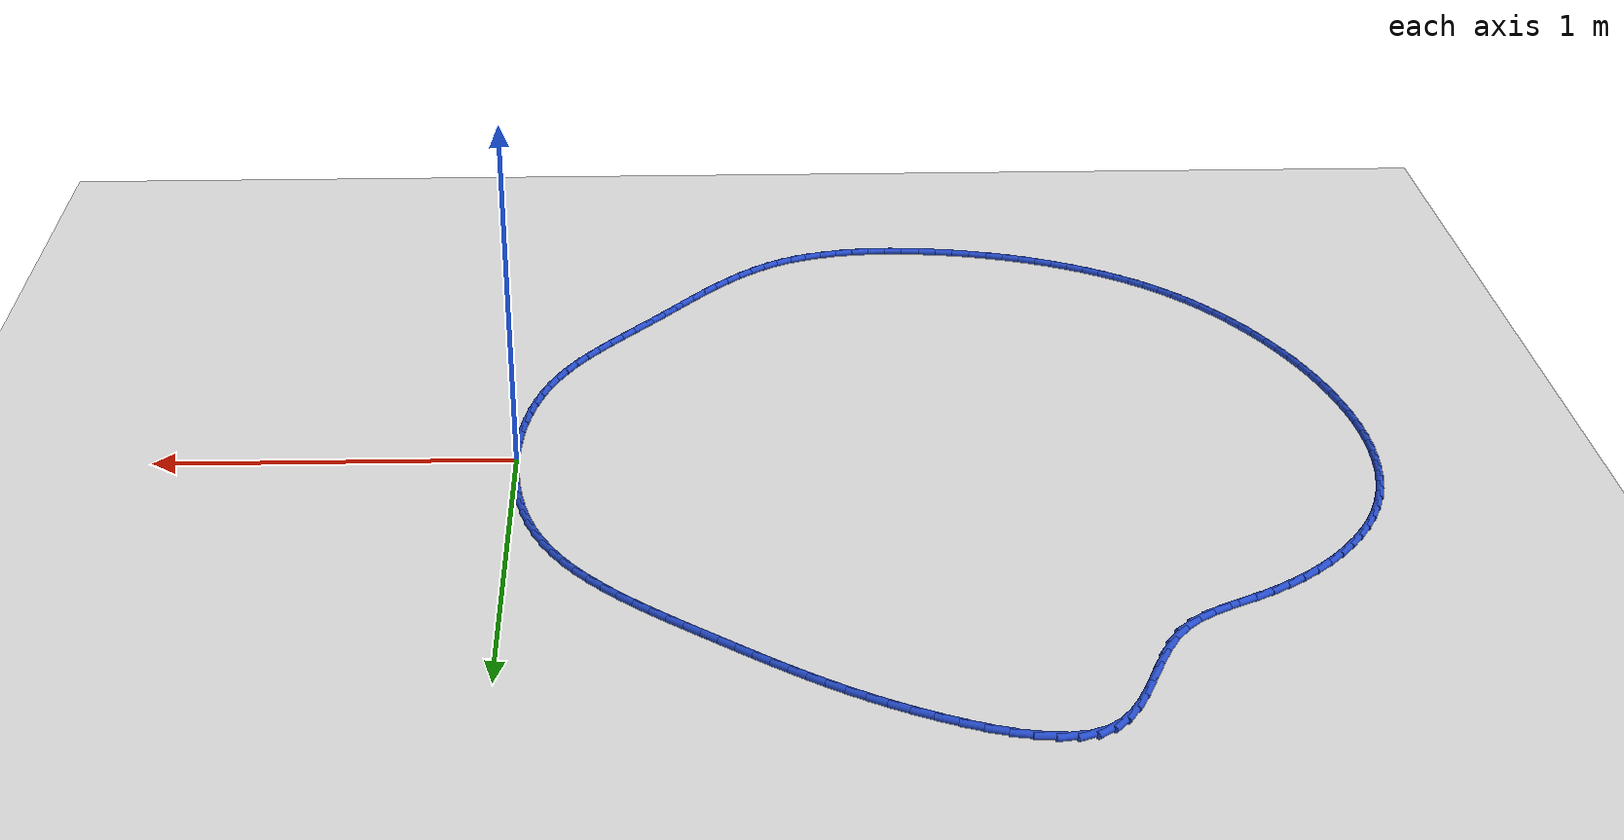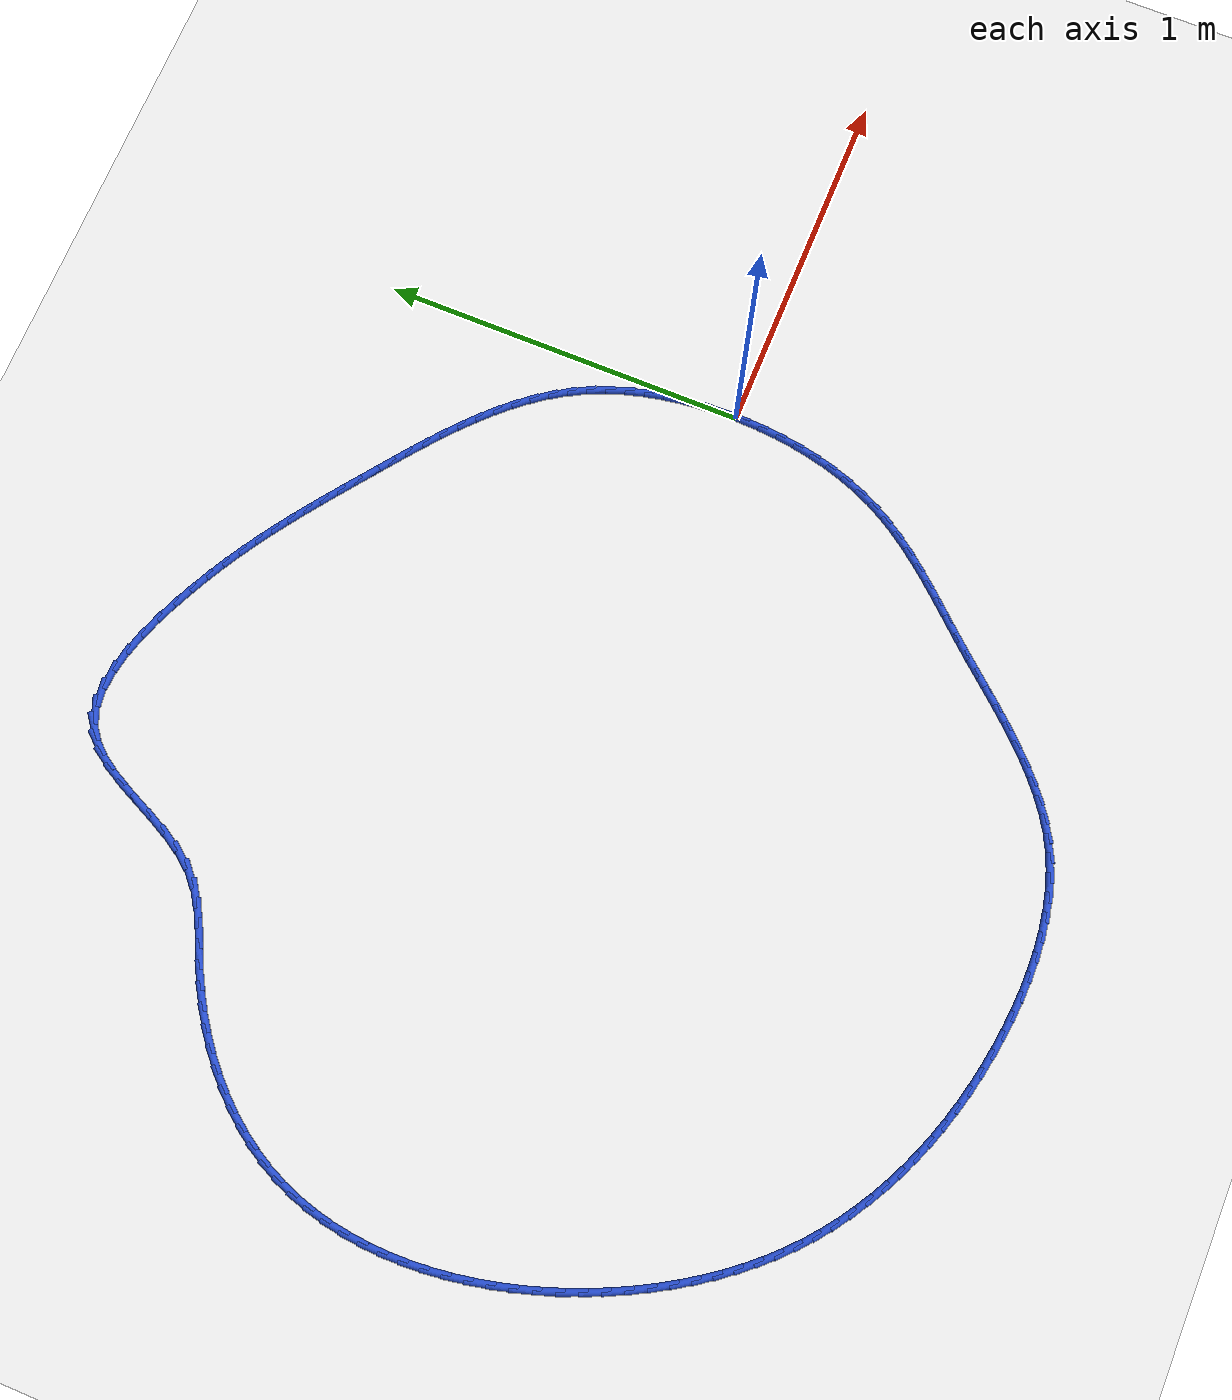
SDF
<sdf version="1.6">
 <world name="default">
  <light name="sun" type="directional">
   <pose>0 0 10 0 -0 0</pose>
   <diffuse>0.8 0.8 0.8 1</diffuse>
   <specular>0.2 0.2 0.2 1</specular>
   <attenuation>
    <range>1000</range>
    <constant>0.9</constant>
    <linear>0.01</linear>
    <quadratic>0.001</quadratic>
   </attenuation>
   <direction>-0.5 0.1 -0.9</direction>
  </light>
  <model name="ground_plane">
   <static>1</static>
   <link name="link">
    <collision name="collision">
     <geometry><plane><normal>0 0 1</normal><size>100 100</size></plane></geometry>
     <surface><friction><ode><mu>100</mu><mu2>50</mu2></ode></friction></surface>
    </collision>
    <visual name="visual">
     <cast_shadows>0</cast_shadows>
     <geometry><plane><normal>0 0 1</normal><size>100 100</size></plane></geometry>
     <material>
      <script><uri>file://media/materials/scripts/gazebo.material</uri><name>Gazebo/WhiteGlow</name></script>
     </material>
    </visual>
   </link>
  </model>
  <gravity>0 0 -9.8</gravity>
  <magnetic_field>6e-06 2.3e-05 -4.2e-05</magnetic_field>
  <atmosphere type="adiabatic"/>
  <physics name="default_physics" default="0" type="ode">
   <max_step_size>0.001</max_step_size>
   <real_time_factor>1</real_time_factor>
   <real_time_update_rate>1000</real_time_update_rate>
  </physics>
  <scene><ambient>0.4 0.4 0.4 1</ambient><background>0.7 0.7 0.7 1</background><shadows>1</shadows></scene>
  <spherical_coordinates>
   <surface_model>EARTH_WGS84</surface_model>
   <latitude_deg>0</latitude_deg>
   <longitude_deg>0</longitude_deg>
   <elevation>0</elevation>
   <heading_deg>0</heading_deg>
  </spherical_coordinates>
  <model name="line">
   <link name="link_0">
    <pose>-6.938893903907228e-18 -5.551115123125783e-17 0.01 0 1.57 -1.5536091324365837</pose>
    <collision name="collision">
     <geometry><cylinder><radius>0.01</radius><length>0.08</length></cylinder></geometry>
    </collision>
    <visual name="visual">
     <material>
      <script><name>Gazebo/Blue</name><uri>file://media/materials/scripts/gazebo.material</uri></script>
     </material>
     <geometry><cylinder><radius>0.01</radius><length>0.08</length></cylinder></geometry>
    </visual>
   </link>
   <link name="link_1">
    <pose>-0.0009261721991384688 0.05388203455751325 0.01 0 1.57 -1.506277487060093</pose>
    <collision name="collision">
     <geometry><cylinder><radius>0.01</radius><length>0.08</length></cylinder></geometry>
    </collision>
    <visual name="visual">
     <material>
      <script><name>Gazebo/Blue</name><uri>file://media/materials/scripts/gazebo.material</uri></script>
     </material>
     <geometry><cylinder><radius>0.01</radius><length>0.08</length></cylinder></geometry>
    </visual>
   </link>
   <link name="link_2">
    <pose>-0.004393588145102005 0.1075501317525404 0.01 0 1.57 -1.4556395476896575</pose>
    <collision name="collision">
     <geometry><cylinder><radius>0.01</radius><length>0.08</length></cylinder></geometry>
    </collision>
    <visual name="visual">
     <material>
      <script><name>Gazebo/Blue</name><uri>file://media/materials/scripts/gazebo.material</uri></script>
     </material>
     <geometry><cylinder><radius>0.01</radius><length>0.08</length></cylinder></geometry>
    </visual>
   </link>
   <link name="link_3">
    <pose>-0.010547140231037505 0.16075001396793595 0.01 0 1.57 -1.401231748263885</pose>
    <collision name="collision">
     <geometry><cylinder><radius>0.01</radius><length>0.08</length></cylinder></geometry>
    </collision>
    <visual name="visual">
     <material>
      <script><name>Gazebo/Blue</name><uri>file://media/materials/scripts/gazebo.material</uri></script>
     </material>
     <geometry><cylinder><radius>0.01</radius><length>0.08</length></cylinder></geometry>
    </visual>
   </link>
   <link name="link_4">
    <pose>-0.019531720850091853 0.2132274035865544 0.01 0 1.57 -1.3426015674663332</pose>
    <collision name="collision">
     <geometry><cylinder><radius>0.01</radius><length>0.08</length></cylinder></geometry>
    </collision>
    <visual name="visual">
     <material>
      <script><name>Gazebo/Blue</name><uri>file://media/materials/scripts/gazebo.material</uri></script>
     </material>
     <geometry><cylinder><radius>0.01</radius><length>0.08</length></cylinder></geometry>
    </visual>
   </link>
   <link name="link_5">
    <pose>-0.03149222239541193 0.2647280229912505 0.01 0 1.57 -1.2793314403193823</pose>
    <collision name="collision">
     <geometry><cylinder><radius>0.01</radius><length>0.08</length></cylinder></geometry>
    </collision>
    <visual name="visual">
     <material>
      <script><name>Gazebo/Blue</name><uri>file://media/materials/scripts/gazebo.material</uri></script>
     </material>
     <geometry><cylinder><radius>0.01</radius><length>0.08</length></cylinder></geometry>
    </visual>
   </link>
   <link name="link_6">
    <pose>-0.046573537260144626 0.3149975945648787 0.01 0 1.57 -1.2110748103025246</pose>
    <collision name="collision">
     <geometry><cylinder><radius>0.01</radius><length>0.08</length></cylinder></geometry>
    </collision>
    <visual name="visual">
     <material>
      <script><name>Gazebo/Blue</name><uri>file://media/materials/scripts/gazebo.material</uri></script>
     </material>
     <geometry><cylinder><radius>0.01</radius><length>0.08</length></cylinder></geometry>
    </visual>
   </link>
   <link name="link_7">
    <pose>-0.0649205578374368 0.3637818406902935 0.01 0 1.57 -1.137605416900079</pose>
    <collision name="collision">
     <geometry><cylinder><radius>0.01</radius><length>0.08</length></cylinder></geometry>
    </collision>
    <visual name="visual">
     <material>
      <script><name>Gazebo/Blue</name><uri>file://media/materials/scripts/gazebo.material</uri></script>
     </material>
     <geometry><cylinder><radius>0.01</radius><length>0.08</length></cylinder></geometry>
    </visual>
   </link>
   <link name="link_8">
    <pose>-0.08667817652043538 0.4108264837503497 0.01 0 1.57 -1.0591342732809301</pose>
    <collision name="collision">
     <geometry><cylinder><radius>0.01</radius><length>0.08</length></cylinder></geometry>
    </collision>
    <visual name="visual">
     <material>
      <script><name>Gazebo/Blue</name><uri>file://media/materials/scripts/gazebo.material</uri></script>
     </material>
     <geometry><cylinder><radius>0.01</radius><length>0.08</length></cylinder></geometry>
    </visual>
   </link>
   <link name="link_9">
    <pose>-0.1119806879437011 0.45588540024555446 0.01 0 1.57 -0.9819720805931468</pose>
    <collision name="collision">
     <geometry><cylinder><radius>0.01</radius><length>0.08</length></cylinder></geometry>
    </collision>
    <visual name="visual">
     <material>
      <script><name>Gazebo/Blue</name><uri>file://media/materials/scripts/gazebo.material</uri></script>
     </material>
     <geometry><cylinder><radius>0.01</radius><length>0.08</length></cylinder></geometry>
    </visual>
   </link>
   <link name="link_10">
    <pose>-0.14071172585937933 0.4989053299417503 0.01 0 1.57 -0.9127349507992571</pose>
    <collision name="collision">
     <geometry><cylinder><radius>0.01</radius><length>0.08</length></cylinder></geometry>
    </collision>
    <visual name="visual">
     <material>
      <script><name>Gazebo/Blue</name><uri>file://media/materials/scripts/gazebo.material</uri></script>
     </material>
     <geometry><cylinder><radius>0.01</radius><length>0.08</length></cylinder></geometry>
    </visual>
   </link>
   <link name="link_11">
    <pose>-0.17250036167070532 0.5400288777328729 0.01 0 1.57 -0.8518553412091386</pose>
    <collision name="collision">
     <geometry><cylinder><radius>0.01</radius><length>0.08</length></cylinder></geometry>
    </collision>
    <visual name="visual">
     <material>
      <script><name>Gazebo/Blue</name><uri>file://media/materials/scripts/gazebo.material</uri></script>
     </material>
     <geometry><cylinder><radius>0.01</radius><length>0.08</length></cylinder></geometry>
    </visual>
   </link>
   <link name="link_12">
    <pose>-0.20696428867067962 0.5794074030479577 0.01 0 1.57 -0.7991875539620596</pose>
    <collision name="collision">
     <geometry><cylinder><radius>0.01</radius><length>0.08</length></cylinder></geometry>
    </collision>
    <visual name="visual">
     <material>
      <script><name>Gazebo/Blue</name><uri>file://media/materials/scripts/gazebo.material</uri></script>
     </material>
     <geometry><cylinder><radius>0.01</radius><length>0.08</length></cylinder></geometry>
    </visual>
   </link>
   <link name="link_13">
    <pose>-0.24372120015230236 0.6171922653160394 0.01 0 1.57 -0.7544118702482225</pose>
    <collision name="collision">
     <geometry><cylinder><radius>0.01</radius><length>0.08</length></cylinder></geometry>
    </collision>
    <visual name="visual">
     <material>
      <script><name>Gazebo/Blue</name><uri>file://media/materials/scripts/gazebo.material</uri></script>
     </material>
     <geometry><cylinder><radius>0.01</radius><length>0.08</length></cylinder></geometry>
    </visual>
   </link>
   <link name="link_14">
    <pose>-0.2823887894085741 0.6535348239661543 0.01 0 1.57 -0.7171387725169786</pose>
    <collision name="collision">
     <geometry><cylinder><radius>0.01</radius><length>0.08</length></cylinder></geometry>
    </collision>
    <visual name="visual">
     <material>
      <script><name>Gazebo/Blue</name><uri>file://media/materials/scripts/gazebo.material</uri></script>
     </material>
     <geometry><cylinder><radius>0.01</radius><length>0.08</length></cylinder></geometry>
    </visual>
   </link>
   <link name="link_15">
    <pose>-0.3225847497324952 0.6885864384273368 0.01 0 1.57 -0.6869849596414311</pose>
    <collision name="collision">
     <geometry><cylinder><radius>0.01</radius><length>0.08</length></cylinder></geometry>
    </collision>
    <visual name="visual">
     <material>
      <script><name>Gazebo/Blue</name><uri>file://media/materials/scripts/gazebo.material</uri></script>
     </material>
     <geometry><cylinder><radius>0.01</radius><length>0.08</length></cylinder></geometry>
    </visual>
   </link>
   <link name="link_16">
    <pose>-0.36392677441706617 0.7224984681286228 0.01 0 1.57 -0.6636255634197527</pose>
    <collision name="collision">
     <geometry><cylinder><radius>0.01</radius><length>0.08</length></cylinder></geometry>
    </collision>
    <visual name="visual">
     <material>
      <script><name>Gazebo/Blue</name><uri>file://media/materials/scripts/gazebo.material</uri></script>
     </material>
     <geometry><cylinder><radius>0.01</radius><length>0.08</length></cylinder></geometry>
    </visual>
   </link>
   <link name="link_17">
    <pose>-0.4060325567552871 0.7554222724990474 0.01 0 1.57 -0.6468295021096749</pose>
    <collision name="collision">
     <geometry><cylinder><radius>0.01</radius><length>0.08</length></cylinder></geometry>
    </collision>
    <visual name="visual">
     <material>
      <script><name>Gazebo/Blue</name><uri>file://media/materials/scripts/gazebo.material</uri></script>
     </material>
     <geometry><cylinder><radius>0.01</radius><length>0.08</length></cylinder></geometry>
    </visual>
   </link>
   <link name="link_18">
    <pose>-0.4485197900401587 0.7875092109676461 0.01 0 1.57 -0.6364847334885766</pose>
    <collision name="collision">
     <geometry><cylinder><radius>0.01</radius><length>0.08</length></cylinder></geometry>
    </collision>
    <visual name="visual">
     <material>
      <script><name>Gazebo/Blue</name><uri>file://media/materials/scripts/gazebo.material</uri></script>
     </material>
     <geometry><cylinder><radius>0.01</radius><length>0.08</length></cylinder></geometry>
    </visual>
   </link>
   <link name="link_19">
    <pose>-0.4910061675646812 0.8189106429634541 0.01 0 1.57 -0.6325855335935207</pose>
    <collision name="collision">
     <geometry><cylinder><radius>0.01</radius><length>0.08</length></cylinder></geometry>
    </collision>
    <visual name="visual">
     <material>
      <script><name>Gazebo/Blue</name><uri>file://media/materials/scripts/gazebo.material</uri></script>
     </material>
     <geometry><cylinder><radius>0.01</radius><length>0.08</length></cylinder></geometry>
    </visual>
   </link>
   <link name="link_20">
    <pose>-0.5331115301108752 0.8497773365442218 0.01 0 1.57 -0.6318701382126259</pose>
    <collision name="collision">
     <geometry><cylinder><radius>0.01</radius><length>0.08</length></cylinder></geometry>
    </collision>
    <visual name="visual">
     <material>
      <script><name>Gazebo/Blue</name><uri>file://media/materials/scripts/gazebo.material</uri></script>
     </material>
     <geometry><cylinder><radius>0.01</radius><length>0.08</length></cylinder></geometry>
    </visual>
   </link>
   <link name="link_21">
    <pose>-0.5746735964070084 0.8802000609691798 0.01 0 1.57 -0.6280409403933495</pose>
    <collision name="collision">
     <geometry><cylinder><radius>0.01</radius><length>0.08</length></cylinder></geometry>
    </collision>
    <visual name="visual">
     <material>
      <script><name>Gazebo/Blue</name><uri>file://media/materials/scripts/gazebo.material</uri></script>
     </material>
     <geometry><cylinder><radius>0.01</radius><length>0.08</length></cylinder></geometry>
    </visual>
   </link>
   <link name="link_22">
    <pose>-0.6159323556368472 0.9101588090540235 0.01 0 1.57 -0.620353311870208</pose>
    <collision name="collision">
     <geometry><cylinder><radius>0.01</radius><length>0.08</length></cylinder></geometry>
    </collision>
    <visual name="visual">
     <material>
      <script><name>Gazebo/Blue</name><uri>file://media/materials/scripts/gazebo.material</uri></script>
     </material>
     <geometry><cylinder><radius>0.01</radius><length>0.08</length></cylinder></geometry>
    </visual>
   </link>
   <link name="link_23">
    <pose>-0.6571712285526243 0.9396216135149043 0.01 0 1.57 -0.6088348140486063</pose>
    <collision name="collision">
     <geometry><cylinder><radius>0.01</radius><length>0.08</length></cylinder></geometry>
    </collision>
    <visual name="visual">
     <material>
      <script><name>Gazebo/Blue</name><uri>file://media/materials/scripts/gazebo.material</uri></script>
     </material>
     <geometry><cylinder><radius>0.01</radius><length>0.08</length></cylinder></geometry>
    </visual>
   </link>
   <link name="link_24">
    <pose>-0.698673635906571 0.9685565070679718 0.01 0 1.57 -0.5936139801577363</pose>
    <collision name="collision">
     <geometry><cylinder><radius>0.01</radius><length>0.08</length></cylinder></geometry>
    </collision>
    <visual name="visual">
     <material>
      <script><name>Gazebo/Blue</name><uri>file://media/materials/scripts/gazebo.material</uri></script>
     </material>
     <geometry><cylinder><radius>0.01</radius><length>0.08</length></cylinder></geometry>
    </visual>
   </link>
   <link name="link_25">
    <pose>-0.7407229984509203 0.9969315224293777 0.01 0 1.57 -0.574920317152491</pose>
    <collision name="collision">
     <geometry><cylinder><radius>0.01</radius><length>0.08</length></cylinder></geometry>
    </collision>
    <visual name="visual">
     <material>
      <script><name>Gazebo/Blue</name><uri>file://media/materials/scripts/gazebo.material</uri></script>
     </material>
     <geometry><cylinder><radius>0.01</radius><length>0.08</length></cylinder></geometry>
    </visual>
   </link>
   <link name="link_26">
    <pose>-0.783602736937904 1.0247146923152721 0.01 0 1.57 -0.5530784157603751</pose>
    <collision name="collision">
     <geometry><cylinder><radius>0.01</radius><length>0.08</length></cylinder></geometry>
    </collision>
    <visual name="visual">
     <material>
      <script><name>Gazebo/Blue</name><uri>file://media/materials/scripts/gazebo.material</uri></script>
     </material>
     <geometry><cylinder><radius>0.01</radius><length>0.08</length></cylinder></geometry>
    </visual>
   </link>
   <link name="link_27">
    <pose>-0.8275962721197543 1.0518740494418062 0.01 0 1.57 -0.5284957722424849</pose>
    <collision name="collision">
     <geometry><cylinder><radius>0.01</radius><length>0.08</length></cylinder></geometry>
    </collision>
    <visual name="visual">
     <material>
      <script><name>Gazebo/Blue</name><uri>file://media/materials/scripts/gazebo.material</uri></script>
     </material>
     <geometry><cylinder><radius>0.01</radius><length>0.08</length></cylinder></geometry>
    </visual>
   </link>
   <link name="link_28">
    <pose>-0.8729870247487037 1.0783776265251301 0.01 0 1.57 -0.5016446627373364</pose>
    <collision name="collision">
     <geometry><cylinder><radius>0.01</radius><length>0.08</length></cylinder></geometry>
    </collision>
    <visual name="visual">
     <material>
      <script><name>Gazebo/Blue</name><uri>file://media/materials/scripts/gazebo.material</uri></script>
     </material>
     <geometry><cylinder><radius>0.01</radius><length>0.08</length></cylinder></geometry>
    </visual>
   </link>
   <link name="link_29">
    <pose>-0.9200584155769845 1.1041934562813955 0.01 0 1.57 -0.47303929964627917</pose>
    <collision name="collision">
     <geometry><cylinder><radius>0.01</radius><length>0.08</length></cylinder></geometry>
    </collision>
    <visual name="visual">
     <material>
      <script><name>Gazebo/Blue</name><uri>file://media/materials/scripts/gazebo.material</uri></script>
     </material>
     <geometry><cylinder><radius>0.01</radius><length>0.08</length></cylinder></geometry>
    </visual>
   </link>
   <link name="link_30">
    <pose>-0.9690938653568283 1.129289571426752 0.01 0 1.57 -0.4432103240331943</pose>
    <collision name="collision">
     <geometry><cylinder><radius>0.01</radius><length>0.08</length></cylinder></geometry>
    </collision>
    <visual name="visual">
     <material>
      <script><name>Gazebo/Blue</name><uri>file://media/materials/scripts/gazebo.material</uri></script>
     </material>
     <geometry><cylinder><radius>0.01</radius><length>0.08</length></cylinder></geometry>
    </visual>
   </link>
   <link name="link_31">
    <pose>-1.0203767948404678 1.1536340046773508 0.01 0 1.57 -0.412032980412588</pose>
    <collision name="collision">
     <geometry><cylinder><radius>0.01</radius><length>0.08</length></cylinder></geometry>
    </collision>
    <visual name="visual">
     <material>
      <script><name>Gazebo/Blue</name><uri>file://media/materials/scripts/gazebo.material</uri></script>
     </material>
     <geometry><cylinder><radius>0.01</radius><length>0.08</length></cylinder></geometry>
    </visual>
   </link>
   <link name="link_32">
    <pose>-1.0741012057852966 1.1771142780695896 0.01 0 1.57 -0.3732032501812656</pose>
    <collision name="collision">
     <geometry><cylinder><radius>0.01</radius><length>0.08</length></cylinder></geometry>
    </collision>
    <visual name="visual">
     <material>
      <script><name>Gazebo/Blue</name><uri>file://media/materials/scripts/gazebo.material</uri></script>
     </material>
     <geometry><cylinder><radius>0.01</radius><length>0.08</length></cylinder></geometry>
    </visual>
   </link>
   <link name="link_33">
    <pose>-1.1296047001592389 1.1988468321787638 0.01 0 1.57 -0.321072868674369</pose>
    <collision name="collision">
     <geometry><cylinder><radius>0.01</radius><length>0.08</length></cylinder></geometry>
    </collision>
    <visual name="visual">
     <material>
      <script><name>Gazebo/Blue</name><uri>file://media/materials/scripts/gazebo.material</uri></script>
     </material>
     <geometry><cylinder><radius>0.01</radius><length>0.08</length></cylinder></geometry>
    </visual>
   </link>
   <link name="link_34">
    <pose>-1.1857484639909872 1.217519154300365 0.01 0 1.57 -0.2514793703086678</pose>
    <collision name="collision">
     <geometry><cylinder><radius>0.01</radius><length>0.08</length></cylinder></geometry>
    </collision>
    <visual name="visual">
     <material>
      <script><name>Gazebo/Blue</name><uri>file://media/materials/scripts/gazebo.material</uri></script>
     </material>
     <geometry><cylinder><radius>0.01</radius><length>0.08</length></cylinder></geometry>
    </visual>
   </link>
   <link name="link_35">
    <pose>-1.2413885548849541 1.2318141142218775 0.01 0 1.57 -0.15796301768268106</pose>
    <collision name="collision">
     <geometry><cylinder><radius>0.01</radius><length>0.08</length></cylinder></geometry>
    </collision>
    <visual name="visual">
     <material>
      <script><name>Gazebo/Blue</name><uri>file://media/materials/scripts/gazebo.material</uri></script>
     </material>
     <geometry><cylinder><radius>0.01</radius><length>0.08</length></cylinder></geometry>
    </visual>
   </link>
   <link name="link_36">
    <pose>-1.295381030445552 1.2404145817307837 0.01 0 1.57 -0.031021615399808883</pose>
    <collision name="collision">
     <geometry><cylinder><radius>0.01</radius><length>0.08</length></cylinder></geometry>
    </collision>
    <visual name="visual">
     <material>
      <script><name>Gazebo/Blue</name><uri>file://media/materials/scripts/gazebo.material</uri></script>
     </material>
     <geometry><cylinder><radius>0.01</radius><length>0.08</length></cylinder></geometry>
    </visual>
   </link>
   <link name="link_37">
    <pose>-1.3465819482771944 1.2420034266145668 0.01 0 1.57 0.1416421298975791</pose>
    <collision name="collision">
     <geometry><cylinder><radius>0.01</radius><length>0.08</length></cylinder></geometry>
    </collision>
    <visual name="visual">
     <material>
      <script><name>Gazebo/Blue</name><uri>file://media/materials/scripts/gazebo.material</uri></script>
     </material>
     <geometry><cylinder><radius>0.01</radius><length>0.08</length></cylinder></geometry>
    </visual>
   </link>
   <link name="link_38">
    <pose>-1.3938473659842934 1.2352635186607106 0.01 0 1.57 0.37048217148772666</pose>
    <collision name="collision">
     <geometry><cylinder><radius>0.01</radius><length>0.08</length></cylinder></geometry>
    </collision>
    <visual name="visual">
     <material>
      <script><name>Gazebo/Blue</name><uri>file://media/materials/scripts/gazebo.material</uri></script>
     </material>
     <geometry><cylinder><radius>0.01</radius><length>0.08</length></cylinder></geometry>
    </visual>
   </link>
   <link name="link_39">
    <pose>-1.436033341171262 1.2188777276566982 0.01 0 1.57 0.6376230430593908</pose>
    <collision name="collision">
     <geometry><cylinder><radius>0.01</radius><length>0.08</length></cylinder></geometry>
    </collision>
    <visual name="visual">
     <material>
      <script><name>Gazebo/Blue</name><uri>file://media/materials/scripts/gazebo.material</uri></script>
     </material>
     <geometry><cylinder><radius>0.01</radius><length>0.08</length></cylinder></geometry>
    </visual>
   </link>
   <link name="link_40">
    <pose>-1.4723301955175832 1.1919869951354516 0.01 0 1.57 0.8556333521397559</pose>
    <collision name="collision">
     <geometry><cylinder><radius>0.01</radius><length>0.08</length></cylinder></geometry>
    </collision>
    <visual name="visual">
     <material>
      <script><name>Gazebo/Blue</name><uri>file://media/materials/scripts/gazebo.material</uri></script>
     </material>
     <geometry><cylinder><radius>0.01</radius><length>0.08</length></cylinder></geometry>
    </visual>
   </link>
   <link name="link_41">
    <pose>-1.503584659787453 1.1560021870913713 0.01 0 1.57 1.0002856444186612</pose>
    <collision name="collision">
     <geometry><cylinder><radius>0.01</radius><length>0.08</length></cylinder></geometry>
    </collision>
    <visual name="visual">
     <material>
      <script><name>Gazebo/Blue</name><uri>file://media/materials/scripts/gazebo.material</uri></script>
     </material>
     <geometry><cylinder><radius>0.01</radius><length>0.08</length></cylinder></geometry>
    </visual>
   </link>
   <link name="link_42">
    <pose>-1.5311556028205424 1.1130359978026474 0.01 0 1.57 1.0851682611648537</pose>
    <collision name="collision">
     <geometry><cylinder><radius>0.01</radius><length>0.08</length></cylinder></geometry>
    </collision>
    <visual name="visual">
     <material>
      <script><name>Gazebo/Blue</name><uri>file://media/materials/scripts/gazebo.material</uri></script>
     </material>
     <geometry><cylinder><radius>0.01</radius><length>0.08</length></cylinder></geometry>
    </visual>
   </link>
   <link name="link_43">
    <pose>-1.5564020439370692 1.065201327764323 0.01 0 1.57 1.1233142922950623</pose>
    <collision name="collision">
     <geometry><cylinder><radius>0.01</radius><length>0.08</length></cylinder></geometry>
    </collision>
    <visual name="visual">
     <material>
      <script><name>Gazebo/Blue</name><uri>file://media/materials/scripts/gazebo.material</uri></script>
     </material>
     <geometry><cylinder><radius>0.01</radius><length>0.08</length></cylinder></geometry>
    </visual>
   </link>
   <link name="link_44">
    <pose>-1.580683002457248 1.01461107747144 0.01 0 1.57 1.1219654271986914</pose>
    <collision name="collision">
     <geometry><cylinder><radius>0.01</radius><length>0.08</length></cylinder></geometry>
    </collision>
    <visual name="visual">
     <material>
      <script><name>Gazebo/Blue</name><uri>file://media/materials/scripts/gazebo.material</uri></script>
     </material>
     <geometry><cylinder><radius>0.01</radius><length>0.08</length></cylinder></geometry>
    </visual>
   </link>
   <link name="link_45">
    <pose>-1.6053574977012963 0.9633781474190437 0.01 0 1.57 1.082609518846327</pose>
    <collision name="collision">
     <geometry><cylinder><radius>0.01</radius><length>0.08</length></cylinder></geometry>
    </collision>
    <visual name="visual">
     <material>
      <script><name>Gazebo/Blue</name><uri>file://media/materials/scripts/gazebo.material</uri></script>
     </material>
     <geometry><cylinder><radius>0.01</radius><length>0.08</length></cylinder></geometry>
    </visual>
   </link>
   <link name="link_46">
    <pose>-1.6317845489894307 0.9136154381021762 0.01 0 1.57 1.00173372946506</pose>
    <collision name="collision">
     <geometry><cylinder><radius>0.01</radius><length>0.08</length></cylinder></geometry>
    </collision>
    <visual name="visual">
     <material>
      <script><name>Gazebo/Blue</name><uri>file://media/materials/scripts/gazebo.material</uri></script>
     </material>
     <geometry><cylinder><radius>0.01</radius><length>0.08</length></cylinder></geometry>
    </visual>
   </link>
   <link name="link_47">
    <pose>-1.6613231756418678 0.8674358500158817 0.01 0 1.57 0.8720955959826324</pose>
    <collision name="collision">
     <geometry><cylinder><radius>0.01</radius><length>0.08</length></cylinder></geometry>
    </collision>
    <visual name="visual">
     <material>
      <script><name>Gazebo/Blue</name><uri>file://media/materials/scripts/gazebo.material</uri></script>
     </material>
     <geometry><cylinder><radius>0.01</radius><length>0.08</length></cylinder></geometry>
    </visual>
   </link>
   <link name="link_48">
    <pose>-1.6953323087583152 0.8269521494269101 0.01 0 1.57 0.7059501299019851</pose>
    <collision name="collision">
     <geometry><cylinder><radius>0.01</radius><length>0.08</length></cylinder></geometry>
    </collision>
    <visual name="visual">
     <material>
      <script><name>Gazebo/Blue</name><uri>file://media/materials/scripts/gazebo.material</uri></script>
     </material>
     <geometry><cylinder><radius>0.01</radius><length>0.08</length></cylinder></geometry>
    </visual>
   </link>
   <link name="link_49">
    <pose>-1.7346284323983652 0.7934517645809668 0.01 0 1.57 0.5712732659725923</pose>
    <collision name="collision">
     <geometry><cylinder><radius>0.01</radius><length>0.08</length></cylinder></geometry>
    </collision>
    <visual name="visual">
     <material>
      <script><name>Gazebo/Blue</name><uri>file://media/materials/scripts/gazebo.material</uri></script>
     </material>
     <geometry><cylinder><radius>0.01</radius><length>0.08</length></cylinder></geometry>
    </visual>
   </link>
   <link name="link_50">
    <pose>-1.7782021560760837 0.7654440392793062 0.01 0 1.57 0.4868002507982963</pose>
    <collision name="collision">
     <geometry><cylinder><radius>0.01</radius><length>0.08</length></cylinder></geometry>
    </collision>
    <visual name="visual">
     <material>
      <script><name>Gazebo/Blue</name><uri>file://media/materials/scripts/gazebo.material</uri></script>
     </material>
     <geometry><cylinder><radius>0.01</radius><length>0.08</length></cylinder></geometry>
    </visual>
   </link>
   <link name="link_51">
    <pose>-1.8246603291922283 0.740854422879947 0.01 0 1.57 0.451416437090773</pose>
    <collision name="collision">
     <geometry><cylinder><radius>0.01</radius><length>0.08</length></cylinder></geometry>
    </collision>
    <visual name="visual">
     <material>
      <script><name>Gazebo/Blue</name><uri>file://media/materials/scripts/gazebo.material</uri></script>
     </material>
     <geometry><cylinder><radius>0.01</radius><length>0.08</length></cylinder></geometry>
    </visual>
   </link>
   <link name="link_52">
    <pose>-1.8726098011475572 0.7176083647409058 0.01 0 1.57 0.4628664930515197</pose>
    <collision name="collision">
     <geometry><cylinder><radius>0.01</radius><length>0.08</length></cylinder></geometry>
    </collision>
    <visual name="visual">
     <material>
      <script><name>Gazebo/Blue</name><uri>file://media/materials/scripts/gazebo.material</uri></script>
     </material>
     <geometry><cylinder><radius>0.01</radius><length>0.08</length></cylinder></geometry>
    </visual>
   </link>
   <link name="link_53">
    <pose>-1.9206574777970238 0.6936314216186111 0.01 0 1.57 0.5110087323230389</pose>
    <collision name="collision">
     <geometry><cylinder><radius>0.01</radius><length>0.08</length></cylinder></geometry>
    </collision>
    <visual name="visual">
     <material>
      <script><name>Gazebo/Blue</name><uri>file://media/materials/scripts/gazebo.material</uri></script>
     </material>
     <geometry><cylinder><radius>0.01</radius><length>0.08</length></cylinder></geometry>
    </visual>
   </link>
   <link name="link_54">
    <pose>-1.9676411709379482 0.6672884255191486 0.01 0 1.57 0.5658011269243801</pose>
    <collision name="collision">
     <geometry><cylinder><radius>0.01</radius><length>0.08</length></cylinder></geometry>
    </collision>
    <visual name="visual">
     <material>
      <script><name>Gazebo/Blue</name><uri>file://media/materials/scripts/gazebo.material</uri></script>
     </material>
     <geometry><cylinder><radius>0.01</radius><length>0.08</length></cylinder></geometry>
    </visual>
   </link>
   <link name="link_55">
    <pose>-2.013155545488408 0.6383840451204902 0.01 0 1.57 0.6215293335487984</pose>
    <collision name="collision">
     <geometry><cylinder><radius>0.01</radius><length>0.08</length></cylinder></geometry>
    </collision>
    <visual name="visual">
     <material>
      <script><name>Gazebo/Blue</name><uri>file://media/materials/scripts/gazebo.material</uri></script>
     </material>
     <geometry><cylinder><radius>0.01</radius><length>0.08</length></cylinder></geometry>
    </visual>
   </link>
   <link name="link_56">
    <pose>-2.056950096576562 0.6070174979480414 0.01 0 1.57 0.6786666127427716</pose>
    <collision name="collision">
     <geometry><cylinder><radius>0.01</radius><length>0.08</length></cylinder></geometry>
    </collision>
    <visual name="visual">
     <material>
      <script><name>Gazebo/Blue</name><uri>file://media/materials/scripts/gazebo.material</uri></script>
     </material>
     <geometry><cylinder><radius>0.01</radius><length>0.08</length></cylinder></geometry>
    </visual>
   </link>
   <link name="link_57">
    <pose>-2.0987743193305732 0.573288001527207 0.01 0 1.57 0.7376788232629999</pose>
    <collision name="collision">
     <geometry><cylinder><radius>0.01</radius><length>0.08</length></cylinder></geometry>
    </collision>
    <visual name="visual">
     <material>
      <script><name>Gazebo/Blue</name><uri>file://media/materials/scripts/gazebo.material</uri></script>
     </material>
     <geometry><cylinder><radius>0.01</radius><length>0.08</length></cylinder></geometry>
    </visual>
   </link>
   <link name="link_58">
    <pose>-2.1383777088785996 0.5372947733833923 0.01 0 1.57 0.7990205599105303</pose>
    <collision name="collision">
     <geometry><cylinder><radius>0.01</radius><length>0.08</length></cylinder></geometry>
    </collision>
    <visual name="visual">
     <material>
      <script><name>Gazebo/Blue</name><uri>file://media/materials/scripts/gazebo.material</uri></script>
     </material>
     <geometry><cylinder><radius>0.01</radius><length>0.08</length></cylinder></geometry>
    </visual>
   </link>
   <link name="link_59">
    <pose>-2.175509760348804 0.49913703104200213 0.01 0 1.57 0.8631265152240056</pose>
    <collision name="collision">
     <geometry><cylinder><radius>0.01</radius><length>0.08</length></cylinder></geometry>
    </collision>
    <visual name="visual">
     <material>
      <script><name>Gazebo/Blue</name><uri>file://media/materials/scripts/gazebo.material</uri></script>
     </material>
     <geometry><cylinder><radius>0.01</radius><length>0.08</length></cylinder></geometry>
    </visual>
   </link>
   <link name="link_60">
    <pose>-2.209919968869345 0.45891399202844213 0.01 0 1.57 0.9303967077149592</pose>
    <collision name="collision">
     <geometry><cylinder><radius>0.01</radius><length>0.08</length></cylinder></geometry>
    </collision>
    <visual name="visual">
     <material>
      <script><name>Gazebo/Blue</name><uri>file://media/materials/scripts/gazebo.material</uri></script>
     </material>
     <geometry><cylinder><radius>0.01</radius><length>0.08</length></cylinder></geometry>
    </visual>
   </link>
   <link name="link_61">
    <pose>-2.241357829568386 0.4167248738681169 0.01 0 1.57 1.0011743313506876</pose>
    <collision name="collision">
     <geometry><cylinder><radius>0.01</radius><length>0.08</length></cylinder></geometry>
    </collision>
    <visual name="visual">
     <material>
      <script><name>Gazebo/Blue</name><uri>file://media/materials/scripts/gazebo.material</uri></script>
     </material>
     <geometry><cylinder><radius>0.01</radius><length>0.08</length></cylinder></geometry>
    </visual>
   </link>
   <link name="link_62">
    <pose>-2.269572837574086 0.37266889408643217 0.01 0 1.57 1.0757155512853973</pose>
    <collision name="collision">
     <geometry><cylinder><radius>0.01</radius><length>0.08</length></cylinder></geometry>
    </collision>
    <visual name="visual">
     <material>
      <script><name>Gazebo/Blue</name><uri>file://media/materials/scripts/gazebo.material</uri></script>
     </material>
     <geometry><cylinder><radius>0.01</radius><length>0.08</length></cylinder></geometry>
    </visual>
   </link>
   <link name="link_63">
    <pose>-2.2943144880146065 0.3268452702087923 0.01 0 1.57 1.1532939582636539</pose>
    <collision name="collision">
     <geometry><cylinder><radius>0.01</radius><length>0.08</length></cylinder></geometry>
    </collision>
    <visual name="visual">
     <material>
      <script><name>Gazebo/Blue</name><uri>file://media/materials/scripts/gazebo.material</uri></script>
     </material>
     <geometry><cylinder><radius>0.01</radius><length>0.08</length></cylinder></geometry>
    </visual>
   </link>
   <link name="link_64">
    <pose>-2.315376935089175 0.2793624262901538 0.01 0 1.57 1.2291708550274865</pose>
    <collision name="collision">
     <geometry><cylinder><radius>0.01</radius><length>0.08</length></cylinder></geometry>
    </collision>
    <visual name="visual">
     <material>
      <script><name>Gazebo/Blue</name><uri>file://media/materials/scripts/gazebo.material</uri></script>
     </material>
     <geometry><cylinder><radius>0.01</radius><length>0.08</length></cylinder></geometry>
    </visual>
   </link>
   <link name="link_65">
    <pose>-2.3327940947707795 0.23037821360826066 0.01 0 1.57 1.3015004724872115</pose>
    <collision name="collision">
     <geometry><cylinder><radius>0.01</radius><length>0.08</length></cylinder></geometry>
    </collision>
    <visual name="visual">
     <material>
      <script><name>Gazebo/Blue</name><uri>file://media/materials/scripts/gazebo.material</uri></script>
     </material>
     <geometry><cylinder><radius>0.01</radius><length>0.08</length></cylinder></geometry>
    </visual>
   </link>
   <link name="link_66">
    <pose>-2.3466800000627344 0.1800669996779746 0.01 0 1.57 1.3701150978979297</pose>
    <collision name="collision">
     <geometry><cylinder><radius>0.01</radius><length>0.08</length></cylinder></geometry>
    </collision>
    <visual name="visual">
     <material>
      <script><name>Gazebo/Blue</name><uri>file://media/materials/scripts/gazebo.material</uri></script>
     </material>
     <geometry><cylinder><radius>0.01</radius><length>0.08</length></cylinder></geometry>
    </visual>
   </link>
   <link name="link_67">
    <pose>-2.357148740398424 0.12860316364729565 0.01 0 1.57 1.434997694866669</pose>
    <collision name="collision">
     <geometry><cylinder><radius>0.01</radius><length>0.08</length></cylinder></geometry>
    </collision>
    <visual name="visual">
     <material>
      <script><name>Gazebo/Blue</name><uri>file://media/materials/scripts/gazebo.material</uri></script>
     </material>
     <geometry><cylinder><radius>0.01</radius><length>0.08</length></cylinder></geometry>
    </visual>
   </link>
   <link name="link_68">
    <pose>-2.364314405211234 0.07616108466422299 0.01 0 1.57 1.4962496220048116</pose>
    <collision name="collision">
     <geometry><cylinder><radius>0.01</radius><length>0.08</length></cylinder></geometry>
    </collision>
    <visual name="visual">
     <material>
      <script><name>Gazebo/Blue</name><uri>file://media/materials/scripts/gazebo.material</uri></script>
     </material>
     <geometry><cylinder><radius>0.01</radius><length>0.08</length></cylinder></geometry>
    </visual>
   </link>
   <link name="link_69">
    <pose>-2.368291083934548 0.022915141876756626 0.01 0 1.57 1.554059608281566</pose>
    <collision name="collision">
     <geometry><cylinder><radius>0.01</radius><length>0.08</length></cylinder></geometry>
    </collision>
    <visual name="visual">
     <material>
      <script><name>Gazebo/Blue</name><uri>file://media/materials/scripts/gazebo.material</uri></script>
     </material>
     <geometry><cylinder><radius>0.01</radius><length>0.08</length></cylinder></geometry>
    </visual>
   </link>
   <link name="link_70">
    <pose>-2.369192866001754 -0.030960285567104562 0.01 0 1.57 -1.532916333319428</pose>
    <collision name="collision">
     <geometry><cylinder><radius>0.01</radius><length>0.08</length></cylinder></geometry>
    </collision>
    <visual name="visual">
     <material>
      <script><name>Gazebo/Blue</name><uri>file://media/materials/scripts/gazebo.material</uri></script>
     </material>
     <geometry><cylinder><radius>0.01</radius><length>0.08</length></cylinder></geometry>
    </visual>
   </link>
   <link name="link_71">
    <pose>-2.3671338408462335 -0.08529081851936018 0.01 0 1.57 -1.4812065436259776</pose>
    <collision name="collision">
     <geometry><cylinder><radius>0.01</radius><length>0.08</length></cylinder></geometry>
    </collision>
    <visual name="visual">
     <material>
      <script><name>Gazebo/Blue</name><uri>file://media/materials/scripts/gazebo.material</uri></script>
     </material>
     <geometry><cylinder><radius>0.01</radius><length>0.08</length></cylinder></geometry>
    </visual>
   </link>
   <link name="link_72">
    <pose>-2.3622280979013737 -0.1399020778320112 0.01 0 1.57 -1.4320964205907463</pose>
    <collision name="collision">
     <geometry><cylinder><radius>0.01</radius><length>0.08</length></cylinder></geometry>
    </collision>
    <visual name="visual">
     <material>
      <script><name>Gazebo/Blue</name><uri>file://media/materials/scripts/gazebo.material</uri></script>
     </material>
     <geometry><cylinder><radius>0.01</radius><length>0.08</length></cylinder></geometry>
    </visual>
   </link>
   <link name="link_73">
    <pose>-2.3545897266005595 -0.19461968435705881 0.01 0 1.57 -1.3852695806720274</pose>
    <collision name="collision">
     <geometry><cylinder><radius>0.01</radius><length>0.08</length></cylinder></geometry>
    </collision>
    <visual name="visual">
     <material>
      <script><name>Gazebo/Blue</name><uri>file://media/materials/scripts/gazebo.material</uri></script>
     </material>
     <geometry><cylinder><radius>0.01</radius><length>0.08</length></cylinder></geometry>
    </visual>
   </link>
   <link name="link_74">
    <pose>-2.3443328163771757 -0.24926925894650187 0.01 0 1.57 -1.3404080794999933</pose>
    <collision name="collision">
     <geometry><cylinder><radius>0.01</radius><length>0.08</length></cylinder></geometry>
    </collision>
    <visual name="visual">
     <material>
      <script><name>Gazebo/Blue</name><uri>file://media/materials/scripts/gazebo.material</uri></script>
     </material>
     <geometry><cylinder><radius>0.01</radius><length>0.08</length></cylinder></geometry>
    </visual>
   </link>
   <link name="link_75">
    <pose>-2.3315714566646077 -0.3036764224523416 0.01 0 1.57 -1.2971966300554192</pose>
    <collision name="collision">
     <geometry><cylinder><radius>0.01</radius><length>0.08</length></cylinder></geometry>
    </collision>
    <visual name="visual">
     <material>
      <script><name>Gazebo/Blue</name><uri>file://media/materials/scripts/gazebo.material</uri></script>
     </material>
     <geometry><cylinder><radius>0.01</radius><length>0.08</length></cylinder></geometry>
    </visual>
   </link>
   <link name="link_76">
    <pose>-2.31641973689624 -0.35766679572657845 0.01 0 1.57 -1.2553242483349523</pose>
    <collision name="collision">
     <geometry><cylinder><radius>0.01</radius><length>0.08</length></cylinder></geometry>
    </collision>
    <visual name="visual">
     <material>
      <script><name>Gazebo/Blue</name><uri>file://media/materials/scripts/gazebo.material</uri></script>
     </material>
     <geometry><cylinder><radius>0.01</radius><length>0.08</length></cylinder></geometry>
    </visual>
   </link>
   <link name="link_77">
    <pose>-2.298991746505458 -0.411065999621213 0.01 0 1.57 -1.214483958629442</pose>
    <collision name="collision">
     <geometry><cylinder><radius>0.01</radius><length>0.08</length></cylinder></geometry>
    </collision>
    <visual name="visual">
     <material>
      <script><name>Gazebo/Blue</name><uri>file://media/materials/scripts/gazebo.material</uri></script>
     </material>
     <geometry><cylinder><radius>0.01</radius><length>0.08</length></cylinder></geometry>
    </visual>
   </link>
   <link name="link_78">
    <pose>-2.279401574925646 -0.4636996549882464 0.01 0 1.57 -1.1743710351229162</pose>
    <collision name="collision">
     <geometry><cylinder><radius>0.01</radius><length>0.08</length></cylinder></geometry>
    </collision>
    <visual name="visual">
     <material>
      <script><name>Gazebo/Blue</name><uri>file://media/materials/scripts/gazebo.material</uri></script>
     </material>
     <geometry><cylinder><radius>0.01</radius><length>0.08</length></cylinder></geometry>
    </visual>
   </link>
   <link name="link_79">
    <pose>-2.2577633115901903 -0.5153933826796775 0.01 0 1.57 -1.134680114921873</pose>
    <collision name="collision">
     <geometry><cylinder><radius>0.01</radius><length>0.08</length></cylinder></geometry>
    </collision>
    <visual name="visual">
     <material>
      <script><name>Gazebo/Blue</name><uri>file://media/materials/scripts/gazebo.material</uri></script>
     </material>
     <geometry><cylinder><radius>0.01</radius><length>0.08</length></cylinder></geometry>
    </visual>
   </link>
   <link name="link_80">
    <pose>-2.234191045932475 -0.5659728035475076 0.01 0 1.57 -1.0951014000303425</pose>
    <collision name="collision">
     <geometry><cylinder><radius>0.01</radius><length>0.08</length></cylinder></geometry>
    </collision>
    <visual name="visual">
     <material>
      <script><name>Gazebo/Blue</name><uri>file://media/materials/scripts/gazebo.material</uri></script>
     </material>
     <geometry><cylinder><radius>0.01</radius><length>0.08</length></cylinder></geometry>
    </visual>
   </link>
   <link name="link_81">
    <pose>-2.2087988673858856 -0.6152635384437368 0.01 0 1.57 -1.055316075023826</pose>
    <collision name="collision">
     <geometry><cylinder><radius>0.01</radius><length>0.08</length></cylinder></geometry>
    </collision>
    <visual name="visual">
     <material>
      <script><name>Gazebo/Blue</name><uri>file://media/materials/scripts/gazebo.material</uri></script>
     </material>
     <geometry><cylinder><radius>0.01</radius><length>0.08</length></cylinder></geometry>
    </visual>
   </link>
   <link name="link_82">
    <pose>-2.1817008653838075 -0.6630912082203669 0.01 0 1.57 -1.0149910038278502</pose>
    <collision name="collision">
     <geometry><cylinder><radius>0.01</radius><length>0.08</length></cylinder></geometry>
    </collision>
    <visual name="visual">
     <material>
      <script><name>Gazebo/Blue</name><uri>file://media/materials/scripts/gazebo.material</uri></script>
     </material>
     <geometry><cylinder><radius>0.01</radius><length>0.08</length></cylinder></geometry>
    </visual>
   </link>
   <link name="link_83">
    <pose>-2.1530111293596255 -0.7092814337293966 0.01 0 1.57 -0.9735969219177171</pose>
    <collision name="collision">
     <geometry><cylinder><radius>0.01</radius><length>0.08</length></cylinder></geometry>
    </collision>
    <visual name="visual">
     <material>
      <script><name>Gazebo/Blue</name><uri>file://media/materials/scripts/gazebo.material</uri></script>
     </material>
     <geometry><cylinder><radius>0.01</radius><length>0.08</length></cylinder></geometry>
    </visual>
   </link>
   <link name="link_84">
    <pose>-2.122819601722197 -0.7536785671830484 0.01 0 1.57 -0.9300949378839116</pose>
    <collision name="collision">
     <geometry><cylinder><radius>0.01</radius><length>0.08</length></cylinder></geometry>
    </collision>
    <visual name="visual">
     <material>
      <script><name>Gazebo/Blue</name><uri>file://media/materials/scripts/gazebo.material</uri></script>
     </material>
     <geometry><cylinder><radius>0.01</radius><length>0.08</length></cylinder></geometry>
    </visual>
   </link>
   <link name="link_85">
    <pose>-2.09110328759548 -0.7962145686461586 0.01 0 1.57 -0.8842951386524368</pose>
    <collision name="collision">
     <geometry><cylinder><radius>0.01</radius><length>0.08</length></cylinder></geometry>
    </collision>
    <visual name="visual">
     <material>
      <script><name>Gazebo/Blue</name><uri>file://media/materials/scripts/gazebo.material</uri></script>
     </material>
     <geometry><cylinder><radius>0.01</radius><length>0.08</length></cylinder></geometry>
    </visual>
   </link>
   <link name="link_86">
    <pose>-2.0578062014499436 -0.8368469897347582 0.01 0 1.57 -0.8363257723098917</pose>
    <collision name="collision">
     <geometry><cylinder><radius>0.01</radius><length>0.08</length></cylinder></geometry>
    </collision>
    <visual name="visual">
     <material>
      <script><name>Gazebo/Blue</name><uri>file://media/materials/scripts/gazebo.material</uri></script>
     </material>
     <geometry><cylinder><radius>0.01</radius><length>0.08</length></cylinder></geometry>
    </visual>
   </link>
   <link name="link_87">
    <pose>-2.022872353760147 -0.8755333851645939 0.01 0 1.57 -0.7863709035076141</pose>
    <collision name="collision">
     <geometry><cylinder><radius>0.01</radius><length>0.08</length></cylinder></geometry>
    </collision>
    <visual name="visual">
     <material>
      <script><name>Gazebo/Blue</name><uri>file://media/materials/scripts/gazebo.material</uri></script>
     </material>
     <geometry><cylinder><radius>0.01</radius><length>0.08</length></cylinder></geometry>
    </visual>
   </link>
   <link name="link_88">
    <pose>-1.986245755000648 -0.91223130965141 0.01 0 1.57 -0.7346722261584941</pose>
    <collision name="collision">
     <geometry><cylinder><radius>0.01</radius><length>0.08</length></cylinder></geometry>
    </collision>
    <visual name="visual">
     <material>
      <script><name>Gazebo/Blue</name><uri>file://media/materials/scripts/gazebo.material</uri></script>
     </material>
     <geometry><cylinder><radius>0.01</radius><length>0.08</length></cylinder></geometry>
    </visual>
   </link>
   <link name="link_89">
    <pose>-1.9478704218937657 -0.9468983202177496 0.01 0 1.57 -0.6820828998065551</pose>
    <collision name="collision">
     <geometry><cylinder><radius>0.01</radius><length>0.08</length></cylinder></geometry>
    </collision>
    <visual name="visual">
     <material>
      <script><name>Gazebo/Blue</name><uri>file://media/materials/scripts/gazebo.material</uri></script>
     </material>
     <geometry><cylinder><radius>0.01</radius><length>0.08</length></cylinder></geometry>
    </visual>
   </link>
   <link name="link_90">
    <pose>-1.90772173788481 -0.9795035550988094 0.01 0 1.57 -0.6306733466079936</pose>
    <collision name="collision">
     <geometry><cylinder><radius>0.01</radius><length>0.08</length></cylinder></geometry>
    </collision>
    <visual name="visual">
     <material>
      <script><name>Gazebo/Blue</name><uri>file://media/materials/scripts/gazebo.material</uri></script>
     </material>
     <geometry><cylinder><radius>0.01</radius><length>0.08</length></cylinder></geometry>
    </visual>
   </link>
   <link name="link_91">
    <pose>-1.8658793328129968 -1.0100546423540748 0.01 0 1.57 -0.5808918701263681</pose>
    <collision name="collision">
     <geometry><cylinder><radius>0.01</radius><length>0.08</length></cylinder></geometry>
    </collision>
    <visual name="visual">
     <material>
      <script><name>Gazebo/Blue</name><uri>file://media/materials/scripts/gazebo.material</uri></script>
     </material>
     <geometry><cylinder><radius>0.01</radius><length>0.08</length></cylinder></geometry>
    </visual>
   </link>
   <link name="link_92">
    <pose>-1.8224444654821819 -1.0385671958832785 0.01 0 1.57 -0.5327575339583152</pose>
    <collision name="collision">
     <geometry><cylinder><radius>0.01</radius><length>0.08</length></cylinder></geometry>
    </collision>
    <visual name="visual">
     <material>
      <script><name>Gazebo/Blue</name><uri>file://media/materials/scripts/gazebo.material</uri></script>
     </material>
     <geometry><cylinder><radius>0.01</radius><length>0.08</length></cylinder></geometry>
    </visual>
   </link>
   <link name="link_93">
    <pose>-1.7775183946962179 -1.065056829586155 0.01 0 1.57 -0.4862595987860679</pose>
    <collision name="collision">
     <geometry><cylinder><radius>0.01</radius><length>0.08</length></cylinder></geometry>
    </collision>
    <visual name="visual">
     <material>
      <script><name>Gazebo/Blue</name><uri>file://media/materials/scripts/gazebo.material</uri></script>
     </material>
     <geometry><cylinder><radius>0.01</radius><length>0.08</length></cylinder></geometry>
    </visual>
   </link>
   <link name="link_94">
    <pose>-1.7312023792589593 -1.0895391573624391 0.01 0 1.57 -0.4413621831955111</pose>
    <collision name="collision">
     <geometry><cylinder><radius>0.01</radius><length>0.08</length></cylinder></geometry>
    </collision>
    <visual name="visual">
     <material>
      <script><name>Gazebo/Blue</name><uri>file://media/materials/scripts/gazebo.material</uri></script>
     </material>
     <geometry><cylinder><radius>0.01</radius><length>0.08</length></cylinder></geometry>
    </visual>
   </link>
   <link name="link_95">
    <pose>-1.6835976779742592 -1.1120297931118648 0.01 0 1.57 -0.3980088379372035</pose>
    <collision name="collision">
     <geometry><cylinder><radius>0.01</radius><length>0.08</length></cylinder></geometry>
    </collision>
    <visual name="visual">
     <material>
      <script><name>Gazebo/Blue</name><uri>file://media/materials/scripts/gazebo.material</uri></script>
     </material>
     <geometry><cylinder><radius>0.01</radius><length>0.08</length></cylinder></geometry>
    </visual>
   </link>
   <link name="link_96">
    <pose>-1.6348055496459728 -1.1325443507341653 0.01 0 1.57 -0.35612679574997513</pose>
    <collision name="collision">
     <geometry><cylinder><radius>0.01</radius><length>0.08</length></cylinder></geometry>
    </collision>
    <visual name="visual">
     <material>
      <script><name>Gazebo/Blue</name><uri>file://media/materials/scripts/gazebo.material</uri></script>
     </material>
     <geometry><cylinder><radius>0.01</radius><length>0.08</length></cylinder></geometry>
    </visual>
   </link>
   <link name="link_97">
    <pose>-1.5849272530779532 -1.1510984441290755 0.01 0 1.57 -0.3156307503470803</pose>
    <collision name="collision">
     <geometry><cylinder><radius>0.01</radius><length>0.08</length></cylinder></geometry>
    </collision>
    <visual name="visual">
     <material>
      <script><name>Gazebo/Blue</name><uri>file://media/materials/scripts/gazebo.material</uri></script>
     </material>
     <geometry><cylinder><radius>0.01</radius><length>0.08</length></cylinder></geometry>
    </visual>
   </link>
   <link name="link_98">
    <pose>-1.5340640470740545 -1.1677076871963292 0.01 0 1.57 -0.2764260931148313</pose>
    <collision name="collision">
     <geometry><cylinder><radius>0.01</radius><length>0.08</length></cylinder></geometry>
    </collision>
    <visual name="visual">
     <material>
      <script><name>Gazebo/Blue</name><uri>file://media/materials/scripts/gazebo.material</uri></script>
     </material>
     <geometry><cylinder><radius>0.01</radius><length>0.08</length></cylinder></geometry>
    </visual>
   </link>
   <link name="link_99">
    <pose>-1.4823171904381311 -1.182387693835661 0.01 0 1.57 -0.23841159208166013</pose>
    <collision name="collision">
     <geometry><cylinder><radius>0.01</radius><length>0.08</length></cylinder></geometry>
    </collision>
    <visual name="visual">
     <material>
      <script><name>Gazebo/Blue</name><uri>file://media/materials/scripts/gazebo.material</uri></script>
     </material>
     <geometry><cylinder><radius>0.01</radius><length>0.08</length></cylinder></geometry>
    </visual>
   </link>
   <link name="link_100">
    <pose>-1.4297879419740351 -1.1951540779468044 0.01 0 1.57 -0.2014815358435118</pose>
    <collision name="collision">
     <geometry><cylinder><radius>0.01</radius><length>0.08</length></cylinder></geometry>
    </collision>
    <visual name="visual">
     <material>
      <script><name>Gazebo/Blue</name><uri>file://media/materials/scripts/gazebo.material</uri></script>
     </material>
     <geometry><cylinder><radius>0.01</radius><length>0.08</length></cylinder></geometry>
    </visual>
   </link>
   <link name="link_101">
    <pose>-1.3765775604856227 -1.2060224534294943 0.01 0 1.57 -0.16552738826390057</pose>
    <collision name="collision">
     <geometry><cylinder><radius>0.01</radius><length>0.08</length></cylinder></geometry>
    </collision>
    <visual name="visual">
     <material>
      <script><name>Gazebo/Blue</name><uri>file://media/materials/scripts/gazebo.material</uri></script>
     </material>
     <geometry><cylinder><radius>0.01</radius><length>0.08</length></cylinder></geometry>
    </visual>
   </link>
   <link name="link_102">
    <pose>-1.3227873047767469 -1.215008434183464 0.01 0 1.57 -0.1303063030385078</pose>
    <collision name="collision">
     <geometry><cylinder><radius>0.01</radius><length>0.08</length></cylinder></geometry>
    </collision>
    <visual name="visual">
     <material>
      <script><name>Gazebo/Blue</name><uri>file://media/materials/scripts/gazebo.material</uri></script>
     </material>
     <geometry><cylinder><radius>0.01</radius><length>0.08</length></cylinder></geometry>
    </visual>
   </link>
   <link name="link_103">
    <pose>-1.2685239433596973 -1.2221195863218242 0.01 0 1.57 -0.09350771259222046</pose>
    <collision name="collision">
     <geometry><cylinder><radius>0.01</radius><length>0.08</length></cylinder></geometry>
    </collision>
    <visual name="visual">
     <material>
      <script><name>Gazebo/Blue</name><uri>file://media/materials/scripts/gazebo.material</uri></script>
     </material>
     <geometry><cylinder><radius>0.01</radius><length>0.08</length></cylinder></geometry>
    </visual>
   </link>
   <link name="link_104">
    <pose>-1.2139825123721713 -1.227234547354034 0.01 0 1.57 -0.05299225513984192</pose>
    <collision name="collision">
     <geometry><cylinder><radius>0.01</radius><length>0.08</length></cylinder></geometry>
    </collision>
    <visual name="visual">
     <material>
      <script><name>Gazebo/Blue</name><uri>file://media/materials/scripts/gazebo.material</uri></script>
     </material>
     <geometry><cylinder><radius>0.01</radius><length>0.08</length></cylinder></geometry>
    </visual>
   </link>
   <link name="link_105">
    <pose>-1.1594291052632297 -1.2301281645279447 0.01 0 1.57 -0.0081802412389</pose>
    <collision name="collision">
     <geometry><cylinder><radius>0.01</radius><length>0.08</length></cylinder></geometry>
    </collision>
    <visual name="visual">
     <material>
      <script><name>Gazebo/Blue</name><uri>file://media/materials/scripts/gazebo.material</uri></script>
     </material>
     <geometry><cylinder><radius>0.01</radius><length>0.08</length></cylinder></geometry>
    </visual>
   </link>
   <link name="link_106">
    <pose>-1.1051318322915935 -1.2305723392270274 0.01 0 1.57 0.041509351207022066</pose>
    <collision name="collision">
     <geometry><cylinder><radius>0.01</radius><length>0.08</length></cylinder></geometry>
    </collision>
    <visual name="visual">
     <material>
      <script><name>Gazebo/Blue</name><uri>file://media/materials/scripts/gazebo.material</uri></script>
     </material>
     <geometry><cylinder><radius>0.01</radius><length>0.08</length></cylinder></geometry>
    </visual>
   </link>
   <link name="link_107">
    <pose>-1.0513588037159844 -1.228338972834752 0.01 0 1.57 0.09669525145830037</pose>
    <collision name="collision">
     <geometry><cylinder><radius>0.01</radius><length>0.08</length></cylinder></geometry>
    </collision>
    <visual name="visual">
     <material>
      <script><name>Gazebo/Blue</name><uri>file://media/materials/scripts/gazebo.material</uri></script>
     </material>
     <geometry><cylinder><radius>0.01</radius><length>0.08</length></cylinder></geometry>
    </visual>
   </link>
   <link name="link_108">
    <pose>-0.9983781297951242 -1.2231999667345885 0.01 0 1.57 0.15800750637988495</pose>
    <collision name="collision">
     <geometry><cylinder><radius>0.01</radius><length>0.08</length></cylinder></geometry>
    </collision>
    <visual name="visual">
     <material>
      <script><name>Gazebo/Blue</name><uri>file://media/materials/scripts/gazebo.material</uri></script>
     </material>
     <geometry><cylinder><radius>0.01</radius><length>0.08</length></cylinder></geometry>
    </visual>
   </link>
   <link name="link_109">
    <pose>-0.9464579207877342 -1.2149272223100078 0.01 0 1.57 0.22604033309905433</pose>
    <collision name="collision">
     <geometry><cylinder><radius>0.01</radius><length>0.08</length></cylinder></geometry>
    </collision>
    <visual name="visual">
     <material>
      <script><name>Gazebo/Blue</name><uri>file://media/materials/scripts/gazebo.material</uri></script>
     </material>
     <geometry><cylinder><radius>0.01</radius><length>0.08</length></cylinder></geometry>
    </visual>
   </link>
   <link name="link_110">
    <pose>-0.8958662869525376 -1.2032926409444795 0.01 0 1.57 0.30127742309918565</pose>
    <collision name="collision">
     <geometry><cylinder><radius>0.01</radius><length>0.08</length></cylinder></geometry>
    </collision>
    <visual name="visual">
     <material>
      <script><name>Gazebo/Blue</name><uri>file://media/materials/scripts/gazebo.material</uri></script>
     </material>
     <geometry><cylinder><radius>0.01</radius><length>0.08</length></cylinder></geometry>
    </visual>
   </link>
   <link name="link_111">
    <pose>-0.8468713385482555 -1.1880681240214745 0.01 0 1.57 0.38398581233174556</pose>
    <collision name="collision">
     <geometry><cylinder><radius>0.01</radius><length>0.08</length></cylinder></geometry>
    </collision>
    <visual name="visual">
     <material>
      <script><name>Gazebo/Blue</name><uri>file://media/materials/scripts/gazebo.material</uri></script>
     </material>
     <geometry><cylinder><radius>0.01</radius><length>0.08</length></cylinder></geometry>
    </visual>
   </link>
   <link name="link_112">
    <pose>-0.7997411858336101 -1.1690255729244636 0.01 0 1.57 0.47322306624549704</pose>
    <collision name="collision">
     <geometry><cylinder><radius>0.01</radius><length>0.08</length></cylinder></geometry>
    </collision>
    <visual name="visual">
     <material>
      <script><name>Gazebo/Blue</name><uri>file://media/materials/scripts/gazebo.material</uri></script>
     </material>
     <geometry><cylinder><radius>0.01</radius><length>0.08</length></cylinder></geometry>
    </visual>
   </link>
   <link name="link_113">
    <pose>-0.7547173278151074 -1.1459721297073622 0.01 0 1.57 0.5586134579030667</pose>
    <collision name="collision">
     <geometry><cylinder><radius>0.01</radius><length>0.08</length></cylinder></geometry>
    </collision>
    <visual name="visual">
     <material>
      <script><name>Gazebo/Blue</name><uri>file://media/materials/scripts/gazebo.material</uri></script>
     </material>
     <geometry><cylinder><radius>0.01</radius><length>0.08</length></cylinder></geometry>
    </visual>
   </link>
   <link name="link_114">
    <pose>-0.711741763805451 -1.1191115569935757 0.01 0 1.57 0.6330632782630781</pose>
    <collision name="collision">
     <geometry><cylinder><radius>0.01</radius><length>0.08</length></cylinder></geometry>
    </collision>
    <visual name="visual">
     <material>
      <script><name>Gazebo/Blue</name><uri>file://media/materials/scripts/gazebo.material</uri></script>
     </material>
     <geometry><cylinder><radius>0.01</radius><length>0.08</length></cylinder></geometry>
    </visual>
   </link>
   <link name="link_115">
    <pose>-0.6705678468932826 -1.0888974372706557 0.01 0 1.57 0.6961065527368835</pose>
    <collision name="collision">
     <geometry><cylinder><radius>0.01</radius><length>0.08</length></cylinder></geometry>
    </collision>
    <visual name="visual">
     <material>
      <script><name>Gazebo/Blue</name><uri>file://media/materials/scripts/gazebo.material</uri></script>
     </material>
     <geometry><cylinder><radius>0.01</radius><length>0.08</length></cylinder></geometry>
    </visual>
   </link>
   <link name="link_116">
    <pose>-0.6309459855463873 -1.0557872525199612 0.01 0 1.57 0.7479079761437735</pose>
    <collision name="collision">
     <geometry><cylinder><radius>0.01</radius><length>0.08</length></cylinder></geometry>
    </collision>
    <visual name="visual">
     <material>
      <script><name>Gazebo/Blue</name><uri>file://media/materials/scripts/gazebo.material</uri></script>
     </material>
     <geometry><cylinder><radius>0.01</radius><length>0.08</length></cylinder></geometry>
    </visual>
   </link>
   <link name="link_117">
    <pose>-0.5926265882325491 -1.0202384847228507 0.01 0 1.57 0.7889189609665751</pose>
    <collision name="collision">
     <geometry><cylinder><radius>0.01</radius><length>0.08</length></cylinder></geometry>
    </collision>
    <visual name="visual">
     <material>
      <script><name>Gazebo/Blue</name><uri>file://media/materials/scripts/gazebo.material</uri></script>
     </material>
     <geometry><cylinder><radius>0.01</radius><length>0.08</length></cylinder></geometry>
    </visual>
   </link>
   <link name="link_118">
    <pose>-0.5553600634195544 -0.9827086158606851 0.01 0 1.57 0.8196849888727429</pose>
    <collision name="collision">
     <geometry><cylinder><radius>0.01</radius><length>0.08</length></cylinder></geometry>
    </collision>
    <visual name="visual">
     <material>
      <script><name>Gazebo/Blue</name><uri>file://media/materials/scripts/gazebo.material</uri></script>
     </material>
     <geometry><cylinder><radius>0.01</radius><length>0.08</length></cylinder></geometry>
    </visual>
   </link>
   <link name="link_119">
    <pose>-0.5188968195751867 -0.9436551279148224 0.01 0 1.57 0.8407160745192289</pose>
    <collision name="collision">
     <geometry><cylinder><radius>0.01</radius><length>0.08</length></cylinder></geometry>
    </collision>
    <visual name="visual">
     <material>
      <script><name>Gazebo/Blue</name><uri>file://media/materials/scripts/gazebo.material</uri></script>
     </material>
     <geometry><cylinder><radius>0.01</radius><length>0.08</length></cylinder></geometry>
    </visual>
   </link>
   <link name="link_120">
    <pose>-0.48298726516723156 -0.9035355028666224 0.01 0 1.57 0.852408554376517</pose>
    <collision name="collision">
     <geometry><cylinder><radius>0.01</radius><length>0.08</length></cylinder></geometry>
    </collision>
    <visual name="visual">
     <material>
      <script><name>Gazebo/Blue</name><uri>file://media/materials/scripts/gazebo.material</uri></script>
     </material>
     <geometry><cylinder><radius>0.01</radius><length>0.08</length></cylinder></geometry>
    </visual>
   </link>
   <link name="link_121">
    <pose>-0.44738180866347377 -0.8628072226974443 0.01 0 1.57 0.855002601147895</pose>
    <collision name="collision">
     <geometry><cylinder><radius>0.01</radius><length>0.08</length></cylinder></geometry>
    </collision>
    <visual name="visual">
     <material>
      <script><name>Gazebo/Blue</name><uri>file://media/materials/scripts/gazebo.material</uri></script>
     </material>
     <geometry><cylinder><radius>0.01</radius><length>0.08</length></cylinder></geometry>
    </visual>
   </link>
   <link name="link_122">
    <pose>-0.4118308585316974 -0.8219277693886461 0.01 0 1.57 0.8485629950406899</pose>
    <collision name="collision">
     <geometry><cylinder><radius>0.01</radius><length>0.08</length></cylinder></geometry>
    </collision>
    <visual name="visual">
     <material>
      <script><name>Gazebo/Blue</name><uri>file://media/materials/scripts/gazebo.material</uri></script>
     </material>
     <geometry><cylinder><radius>0.01</radius><length>0.08</length></cylinder></geometry>
    </visual>
   </link>
   <link name="link_123">
    <pose>-0.3760848234275723 -0.7813546247065388 0.01 0 1.57 0.8362648200237897</pose>
    <collision name="collision">
     <geometry><cylinder><radius>0.01</radius><length>0.08</length></cylinder></geometry>
    </collision>
    <visual name="visual">
     <material>
      <script><name>Gazebo/Blue</name><uri>file://media/materials/scripts/gazebo.material</uri></script>
     </material>
     <geometry><cylinder><radius>0.01</radius><length>0.08</length></cylinder></geometry>
    </visual>
   </link>
   <link name="link_124">
    <pose>-0.3400113496667749 -0.7414110810175384 0.01 0 1.57 0.8307174092500438</pose>
    <collision name="collision">
     <geometry><cylinder><radius>0.01</radius><length>0.08</length></cylinder></geometry>
    </collision>
    <visual name="visual">
     <material>
      <script><name>Gazebo/Blue</name><uri>file://media/materials/scripts/gazebo.material</uri></script>
     </material>
     <geometry><cylinder><radius>0.01</radius><length>0.08</length></cylinder></geometry>
    </visual>
   </link>
   <link name="link_125">
    <pose>-0.3039306709004583 -0.7019024024116403 0.01 0 1.57 0.8351237623532022</pose>
    <collision name="collision">
     <geometry><cylinder><radius>0.01</radius><length>0.08</length></cylinder></geometry>
    </collision>
    <visual name="visual">
     <material>
      <script><name>Gazebo/Blue</name><uri>file://media/materials/scripts/gazebo.material</uri></script>
     </material>
     <geometry><cylinder><radius>0.01</radius><length>0.08</length></cylinder></geometry>
    </visual>
   </link>
   <link name="link_126">
    <pose>-0.26827221856015426 -0.6625088659685424 0.01 0 1.57 0.8497046216174723</pose>
    <collision name="collision">
     <geometry><cylinder><radius>0.01</radius><length>0.08</length></cylinder></geometry>
    </collision>
    <visual name="visual">
     <material>
      <script><name>Gazebo/Blue</name><uri>file://media/materials/scripts/gazebo.material</uri></script>
     </material>
     <geometry><cylinder><radius>0.01</radius><length>0.08</length></cylinder></geometry>
    </visual>
   </link>
   <link name="link_127">
    <pose>-0.23346542407739612 -0.622910748767945 0.01 0 1.57 0.8747304905999064</pose>
    <collision name="collision">
     <geometry><cylinder><radius>0.01</radius><length>0.08</length></cylinder></geometry>
    </collision>
    <visual name="visual">
     <material>
      <script><name>Gazebo/Blue</name><uri>file://media/materials/scripts/gazebo.material</uri></script>
     </material>
     <geometry><cylinder><radius>0.01</radius><length>0.08</length></cylinder></geometry>
    </visual>
   </link>
   <link name="link_128">
    <pose>-0.19993971888371573 -0.582788327889546 0.01 0 1.57 0.9104776572240305</pose>
    <collision name="collision">
     <geometry><cylinder><radius>0.01</radius><length>0.08</length></cylinder></geometry>
    </collision>
    <visual name="visual">
     <material>
      <script><name>Gazebo/Blue</name><uri>file://media/materials/scripts/gazebo.material</uri></script>
     </material>
     <geometry><cylinder><radius>0.01</radius><length>0.08</length></cylinder></geometry>
    </visual>
   </link>
   <link name="link_129">
    <pose>-0.16812453441064526 -0.5418218804130445 0.01 0 1.57 0.9571437244117205</pose>
    <collision name="collision">
     <geometry><cylinder><radius>0.01</radius><length>0.08</length></cylinder></geometry>
    </collision>
    <visual name="visual">
     <material>
      <script><name>Gazebo/Blue</name><uri>file://media/materials/scripts/gazebo.material</uri></script>
     </material>
     <geometry><cylinder><radius>0.01</radius><length>0.08</length></cylinder></geometry>
    </visual>
   </link>
   <link name="link_130">
    <pose>-0.13844930208971692 -0.4996916834181391 0.01 0 1.57 1.0147185997044106</pose>
    <collision name="collision">
     <geometry><cylinder><radius>0.01</radius><length>0.08</length></cylinder></geometry>
    </collision>
    <visual name="visual">
     <material>
      <script><name>Gazebo/Blue</name><uri>file://media/materials/scripts/gazebo.material</uri></script>
     </material>
     <geometry><cylinder><radius>0.01</radius><length>0.08</length></cylinder></geometry>
    </visual>
   </link>
   <link name="link_131">
    <pose>-0.1113434533524627 -0.45607801398452824 0.01 0 1.57 1.082515377827218</pose>
    <collision name="collision">
     <geometry><cylinder><radius>0.01</radius><length>0.08</length></cylinder></geometry>
    </collision>
    <visual name="visual">
     <material>
      <script><name>Gazebo/Blue</name><uri>file://media/materials/scripts/gazebo.material</uri></script>
     </material>
     <geometry><cylinder><radius>0.01</radius><length>0.08</length></cylinder></geometry>
    </visual>
   </link>
   <link name="link_132">
    <pose>-0.087225084570951 -0.41067292324429994 0.01 0 1.57 1.1530958039946302</pose>
    <collision name="collision">
     <geometry><cylinder><radius>0.01</radius><length>0.08</length></cylinder></geometry>
    </collision>
    <visual name="visual">
     <material>
      <script><name>Gazebo/Blue</name><uri>file://media/materials/scripts/gazebo.material</uri></script>
     </material>
     <geometry><cylinder><radius>0.01</radius><length>0.08</length></cylinder></geometry>
    </visual>
   </link>
   <link name="link_133">
    <pose>-0.06625869294279833 -0.36343188308836716 0.01 0 1.57 1.2196489799788213</pose>
    <collision name="collision">
     <geometry><cylinder><radius>0.01</radius><length>0.08</length></cylinder></geometry>
    </collision>
    <visual name="visual">
     <material>
      <script><name>Gazebo/Blue</name><uri>file://media/materials/scripts/gazebo.material</uri></script>
     </material>
     <geometry><cylinder><radius>0.01</radius><length>0.08</length></cylinder></geometry>
    </visual>
   </link>
   <link name="link_134">
    <pose>-0.04835906319588794 -0.31456974893445633 0.01 0 1.57 1.2820540291329727</pose>
    <collision name="collision">
     <geometry><cylinder><radius>0.01</radius><length>0.08</length></cylinder></geometry>
    </collision>
    <visual name="visual">
     <material>
      <script><name>Gazebo/Blue</name><uri>file://media/materials/scripts/gazebo.material</uri></script>
     </material>
     <geometry><cylinder><radius>0.01</radius><length>0.08</length></cylinder></geometry>
    </visual>
   </link>
   <link name="link_135">
    <pose>-0.03343042239771041 -0.26431234274589793 0.01 0 1.57 1.3405720328414106</pose>
    <collision name="collision">
     <geometry><cylinder><radius>0.01</radius><length>0.08</length></cylinder></geometry>
    </collision>
    <visual name="visual">
     <material>
      <script><name>Gazebo/Blue</name><uri>file://media/materials/scripts/gazebo.material</uri></script>
     </material>
     <geometry><cylinder><radius>0.01</radius><length>0.08</length></cylinder></geometry>
    </visual>
   </link>
   <link name="link_136">
    <pose>-0.021376997615757058 -0.21288548648602462 0.01 0 1.57 1.3955291776762904</pose>
    <collision name="collision">
     <geometry><cylinder><radius>0.01</radius><length>0.08</length></cylinder></geometry>
    </collision>
    <visual name="visual">
     <material>
      <script><name>Gazebo/Blue</name><uri>file://media/materials/scripts/gazebo.material</uri></script>
     </material>
     <geometry><cylinder><radius>0.01</radius><length>0.08</length></cylinder></geometry>
    </visual>
   </link>
   <link name="link_137">
    <pose>-0.012103015917518509 -0.16051500211816702 0.01 0 1.57 1.447289467889138</pose>
    <collision name="collision">
     <geometry><cylinder><radius>0.01</radius><length>0.08</length></cylinder></geometry>
    </collision>
    <visual name="visual">
     <material>
      <script><name>Gazebo/Blue</name><uri>file://media/materials/scripts/gazebo.material</uri></script>
     </material>
     <geometry><cylinder><radius>0.01</radius><length>0.08</length></cylinder></geometry>
    </visual>
   </link>
   <link name="link_138">
    <pose>-0.005512704370485581 -0.10742671160565638 0.01 0 1.57 1.496235405160228</pose>
    <collision name="collision">
     <geometry><cylinder><radius>0.01</radius><length>0.08</length></cylinder></geometry>
    </collision>
    <visual name="visual">
     <material>
      <script><name>Gazebo/Blue</name><uri>file://media/materials/scripts/gazebo.material</uri></script>
     </material>
     <geometry><cylinder><radius>0.01</radius><length>0.08</length></cylinder></geometry>
    </visual>
   </link>
   <link name="link_139">
    <pose>-0.0015102900421491367 -0.05384643691182401 0.01 0 1.57 1.5427555822377397</pose>
    <collision name="collision">
     <geometry><cylinder><radius>0.01</radius><length>0.08</length></cylinder></geometry>
    </collision>
    <visual name="visual">
     <material>
      <script><name>Gazebo/Blue</name><uri>file://media/materials/scripts/gazebo.material</uri></script>
     </material>
     <geometry><cylinder><radius>0.01</radius><length>0.08</length></cylinder></geometry>
    </visual>
   </link>
   <link name="link_140">
    <pose>-2.2551405187698492e-17 -2.636779683484747e-16 0.01 0 1.57 -1.554354789270873</pose>
    <collision name="collision">
     <geometry><cylinder><radius>0.01</radius><length>0.08</length></cylinder></geometry>
    </collision>
    <visual name="visual">
     <material>
      <script><name>Gazebo/Blue</name><uri>file://media/materials/scripts/gazebo.material</uri></script>
     </material>
     <geometry><cylinder><radius>0.01</radius><length>0.08</length></cylinder></geometry>
    </visual>
   </link>
   <link name="link_141">
    <pose>-0.0008860613115291242 0.05388677716648186 0.01 0 1.57 -1.5543547892708727</pose>
    <collision name="collision">
     <geometry><cylinder><radius>0.01</radius><length>0.08</length></cylinder></geometry>
    </collision>
    <visual name="visual">
     <material>
      <script><name>Gazebo/Blue</name><uri>file://media/materials/scripts/gazebo.material</uri></script>
     </material>
     <geometry><cylinder><radius>0.01</radius><length>0.08</length></cylinder></geometry>
    </visual>
   </link>
  </model>
 </world>
</sdf>
